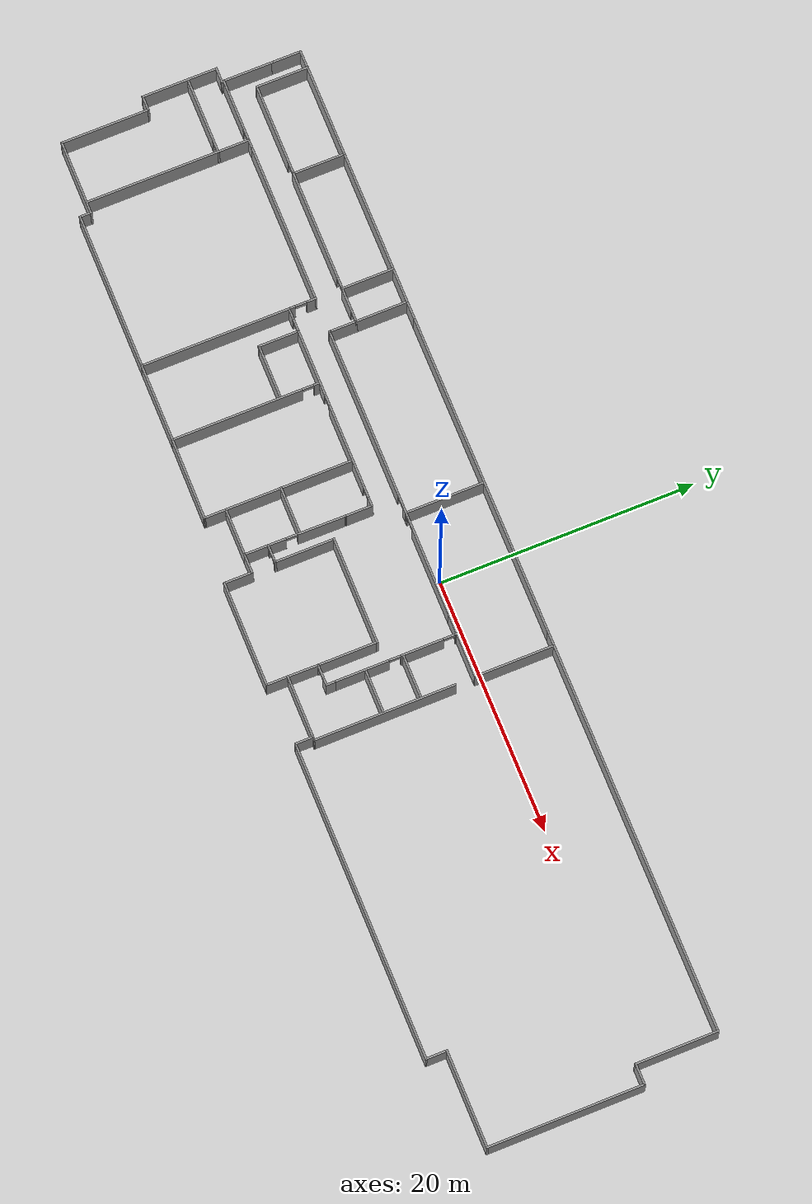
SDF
<?xml version='1.0'?>
<sdf version='1.7'>
  <model name='SMU_4th_Floor'>
    <pose>-0.970671 -4.58081 0 0 -0 0</pose>
    <link name='Wall_10'>
      <pose>-21.9301 2.97041 0 0 -0 1.5708</pose>
      <visual name='Wall_10_Visual_0'>
        <pose>-0.849622 0 1.25 0 -0 0</pose>
        <geometry>
          <box>
            <size>0.550756 0.15 2.5</size>
          </box>
        </geometry>
        <material>
          <script>
            <uri>file://media/materials/scripts/gazebo.material</uri>
            <name>Gazebo/Grey</name>
          </script>
          <ambient>1 1 1 1</ambient>
        </material>
        <meta>
          <layer>0</layer>
        </meta>
      </visual>
      <collision name='Wall_10_Collision_0'>
        <geometry>
          <box>
            <size>0.550756 0.15 2.5</size>
          </box>
        </geometry>
        <pose>-0.849622 0 1.25 0 -0 0</pose>
      </collision>
      <visual name='Wall_10_Visual_1'>
        <pose>0.725378 0 1.25 0 -0 0</pose>
        <geometry>
          <box>
            <size>0.799244 0.15 2.5</size>
          </box>
        </geometry>
        <material>
          <script>
            <uri>file://media/materials/scripts/gazebo.material</uri>
            <name>Gazebo/Grey</name>
          </script>
          <ambient>1 1 1 1</ambient>
        </material>
        <meta>
          <layer>0</layer>
        </meta>
      </visual>
      <collision name='Wall_10_Collision_1'>
        <geometry>
          <box>
            <size>0.799244 0.15 2.5</size>
          </box>
        </geometry>
        <pose>0.725378 0 1.25 0 -0 0</pose>
      </collision>
      <visual name='Wall_10_Visual_2'>
        <pose>-0.124244 0 2.25 0 -0 0</pose>
        <geometry>
          <box>
            <size>0.9 0.15 0.5</size>
          </box>
        </geometry>
        <material>
          <script>
            <uri>file://media/materials/scripts/gazebo.material</uri>
            <name>Gazebo/Grey</name>
          </script>
          <ambient>1 1 1 1</ambient>
        </material>
        <meta>
          <layer>0</layer>
        </meta>
      </visual>
      <collision name='Wall_10_Collision_2'>
        <geometry>
          <box>
            <size>0.9 0.15 0.5</size>
          </box>
        </geometry>
        <pose>-0.124244 0 2.25 0 -0 0</pose>
      </collision>
    </link>
    <link name='Wall_101'>
      <collision name='Wall_101_Collision'>
        <geometry>
          <box>
            <size>1.5 0.15 2.5</size>
          </box>
        </geometry>
        <pose>0 0 1.25 0 -0 0</pose>
      </collision>
      <visual name='Wall_101_Visual'>
        <pose>0 0 1.25 0 -0 0</pose>
        <geometry>
          <box>
            <size>1.5 0.15 2.5</size>
          </box>
        </geometry>
        <material>
          <script>
            <uri>file://media/materials/scripts/gazebo.material</uri>
            <name>Gazebo/Grey</name>
          </script>
          <ambient>1 1 1 1</ambient>
        </material>
        <meta>
          <layer>0</layer>
        </meta>
      </visual>
      <pose>8.74333 -9.19549 0 0 -0 1.5708</pose>
    </link>
    <link name='Wall_102'>
      <collision name='Wall_102_Collision'>
        <geometry>
          <box>
            <size>5 0.15 2.5</size>
          </box>
        </geometry>
        <pose>0 0 1.25 0 -0 0</pose>
      </collision>
      <visual name='Wall_102_Visual'>
        <pose>0 0 1.25 0 -0 0</pose>
        <geometry>
          <box>
            <size>5 0.15 2.5</size>
          </box>
        </geometry>
        <material>
          <script>
            <uri>file://media/materials/scripts/gazebo.material</uri>
            <name>Gazebo/Grey</name>
          </script>
          <ambient>1 1 1 1</ambient>
        </material>
        <meta>
          <layer>0</layer>
        </meta>
      </visual>
      <pose>6.31833 -8.52049 0 0 -0 3.14159</pose>
    </link>
    <link name='Wall_103'>
      <collision name='Wall_103_Collision'>
        <geometry>
          <box>
            <size>2.49105 0.15 2.5</size>
          </box>
        </geometry>
        <pose>0 0 1.25 0 -0 0</pose>
      </collision>
      <visual name='Wall_103_Visual'>
        <pose>0 0 1.25 0 -0 0</pose>
        <geometry>
          <box>
            <size>2.49105 0.15 2.5</size>
          </box>
        </geometry>
        <material>
          <script>
            <uri>file://media/materials/scripts/gazebo.material</uri>
            <name>Gazebo/Grey</name>
          </script>
          <ambient>1 1 1 1</ambient>
        </material>
        <meta>
          <layer>0</layer>
        </meta>
      </visual>
      <pose>3.90663 -7.35004 0 0 -0 1.55943</pose>
    </link>
    <link name='Wall_105'>
      <collision name='Wall_105_Collision'>
        <geometry>
          <box>
            <size>6.25 0.15 2.5</size>
          </box>
        </geometry>
        <pose>0 0 1.25 0 -0 0</pose>
      </collision>
      <visual name='Wall_105_Visual'>
        <pose>0 0 1.25 0 -0 0</pose>
        <geometry>
          <box>
            <size>6.25 0.15 2.5</size>
          </box>
        </geometry>
        <material>
          <script>
            <uri>file://media/materials/scripts/gazebo.material</uri>
            <name>Gazebo/Grey</name>
          </script>
          <ambient>1 1 1 1</ambient>
        </material>
        <meta>
          <layer>0</layer>
        </meta>
      </visual>
      <pose>-4.29599 7.06809 0 0 -0 -1.5708</pose>
    </link>
    <link name='Wall_107'>
      <collision name='Wall_107_Collision'>
        <geometry>
          <box>
            <size>1.6 0.15 2.5</size>
          </box>
        </geometry>
        <pose>0 0 1.25 0 -0 0</pose>
      </collision>
      <visual name='Wall_107_Visual'>
        <pose>0 0 1.25 0 -0 0</pose>
        <geometry>
          <box>
            <size>1.6 0.15 2.5</size>
          </box>
        </geometry>
        <material>
          <script>
            <uri>file://media/materials/scripts/gazebo.material</uri>
            <name>Gazebo/Grey</name>
          </script>
          <ambient>1 1 1 1</ambient>
        </material>
        <meta>
          <layer>0</layer>
        </meta>
      </visual>
      <pose>-5.05507 -8.02959 0 0 -0 0</pose>
    </link>
    <link name='Wall_109'>
      <collision name='Wall_109_Collision'>
        <geometry>
          <box>
            <size>2.3 0.15 2.5</size>
          </box>
        </geometry>
        <pose>0 0 1.25 0 -0 0</pose>
      </collision>
      <visual name='Wall_109_Visual'>
        <pose>0 0 1.25 0 -0 0</pose>
        <geometry>
          <box>
            <size>2.3 0.15 2.5</size>
          </box>
        </geometry>
        <material>
          <script>
            <uri>file://media/materials/scripts/gazebo.material</uri>
            <name>Gazebo/Grey</name>
          </script>
          <ambient>1 1 1 1</ambient>
        </material>
        <meta>
          <layer>0</layer>
        </meta>
      </visual>
      <pose>-4.33007 -9.10459 0 0 -0 -1.5708</pose>
    </link>
    <link name='Wall_11'>
      <collision name='Wall_11_Collision'>
        <geometry>
          <box>
            <size>12.75 0.15 2.5</size>
          </box>
        </geometry>
        <pose>0 0 1.25 0 -0 0</pose>
      </collision>
      <visual name='Wall_11_Visual'>
        <pose>0 0 1.25 0 -0 0</pose>
        <geometry>
          <box>
            <size>12.75 0.15 2.5</size>
          </box>
        </geometry>
        <material>
          <script>
            <uri>file://media/materials/scripts/gazebo.material</uri>
            <name>Gazebo/Grey</name>
          </script>
          <ambient>1 1 1 1</ambient>
        </material>
        <meta>
          <layer>0</layer>
        </meta>
      </visual>
      <pose>-28.2301 4.02041 0 0 -0 3.14159</pose>
    </link>
    <link name='Wall_111'>
      <collision name='Wall_111_Collision'>
        <geometry>
          <box>
            <size>8.3 0.15 2.5</size>
          </box>
        </geometry>
        <pose>0 0 1.25 0 -0 0</pose>
      </collision>
      <visual name='Wall_111_Visual'>
        <pose>0 0 1.25 0 -0 0</pose>
        <geometry>
          <box>
            <size>8.3 0.15 2.5</size>
          </box>
        </geometry>
        <material>
          <script>
            <uri>file://media/materials/scripts/gazebo.material</uri>
            <name>Gazebo/Grey</name>
          </script>
          <ambient>1 1 1 1</ambient>
        </material>
        <meta>
          <layer>0</layer>
        </meta>
      </visual>
      <pose>-0.255066 -10.1796 0 0 -0 0</pose>
    </link>
    <link name='Wall_113'>
      <collision name='Wall_113_Collision'>
        <geometry>
          <box>
            <size>1.8 0.15 2.5</size>
          </box>
        </geometry>
        <pose>0 0 1.25 0 -0 0</pose>
      </collision>
      <visual name='Wall_113_Visual'>
        <pose>0 0 1.25 0 -0 0</pose>
        <geometry>
          <box>
            <size>1.8 0.15 2.5</size>
          </box>
        </geometry>
        <material>
          <script>
            <uri>file://media/materials/scripts/gazebo.material</uri>
            <name>Gazebo/Grey</name>
          </script>
          <ambient>1 1 1 1</ambient>
        </material>
        <meta>
          <layer>0</layer>
        </meta>
      </visual>
      <pose>3.89333 -9.34549 0 0 -0 -1.5708</pose>
    </link>
    <link name='Wall_115'>
      <collision name='Wall_115_Collision'>
        <geometry>
          <box>
            <size>11.11 0.15 2.5</size>
          </box>
        </geometry>
        <pose>0 0 1.25 0 -0 0</pose>
      </collision>
      <visual name='Wall_115_Visual'>
        <pose>0 0 1.25 0 -0 0</pose>
        <geometry>
          <box>
            <size>11.11 0.15 2.5</size>
          </box>
        </geometry>
        <material>
          <script>
            <uri>file://media/materials/scripts/gazebo.material</uri>
            <name>Gazebo/Grey</name>
          </script>
          <ambient>1 1 1 1</ambient>
        </material>
        <meta>
          <layer>0</layer>
        </meta>
      </visual>
      <pose>8.99588 -3.03503 0 0 -0 -1.5708</pose>
    </link>
    <link name='Wall_119'>
      <collision name='Wall_119_Collision'>
        <geometry>
          <box>
            <size>0.402607 0.15 2.5</size>
          </box>
        </geometry>
        <pose>0 0 1.25 0 -0 0</pose>
      </collision>
      <visual name='Wall_119_Visual'>
        <pose>0 0 1.25 0 -0 0</pose>
        <geometry>
          <box>
            <size>0.402607 0.15 2.5</size>
          </box>
        </geometry>
        <material>
          <script>
            <uri>file://media/materials/scripts/gazebo.material</uri>
            <name>Gazebo/Grey</name>
          </script>
          <ambient>1 1 1 1</ambient>
        </material>
        <meta>
          <layer>0</layer>
        </meta>
      </visual>
      <pose>8.86961 -8.51776 0 0 -0 0.02159</pose>
    </link>
    <link name='Wall_122'>
      <collision name='Wall_122_Collision'>
        <geometry>
          <box>
            <size>3.5 0.15 2.5</size>
          </box>
        </geometry>
        <pose>0 0 1.25 0 -0 0</pose>
      </collision>
      <visual name='Wall_122_Visual'>
        <pose>0 0 1.25 0 -0 0</pose>
        <geometry>
          <box>
            <size>3.5 0.15 2.5</size>
          </box>
        </geometry>
        <material>
          <script>
            <uri>file://media/materials/scripts/gazebo.material</uri>
            <name>Gazebo/Grey</name>
          </script>
          <ambient>1 1 1 1</ambient>
        </material>
        <meta>
          <layer>0</layer>
        </meta>
      </visual>
      <pose>7.22208 -3.13125 0 0 -0 0</pose>
    </link>
    <link name='Wall_124'>
      <collision name='Wall_124_Collision'>
        <geometry>
          <box>
            <size>3.5 0.15 2.5</size>
          </box>
        </geometry>
        <pose>0 0 1.25 0 -0 0</pose>
      </collision>
      <visual name='Wall_124_Visual'>
        <pose>0 0 1.25 0 -0 0</pose>
        <geometry>
          <box>
            <size>3.5 0.15 2.5</size>
          </box>
        </geometry>
        <material>
          <script>
            <uri>file://media/materials/scripts/gazebo.material</uri>
            <name>Gazebo/Grey</name>
          </script>
          <ambient>1 1 1 1</ambient>
        </material>
        <meta>
          <layer>0</layer>
        </meta>
      </visual>
      <pose>7.28373 -0.193726 0 0 -0 3.14159</pose>
    </link>
    <link name='Wall_126'>
      <collision name='Wall_126_Collision'>
        <geometry>
          <box>
            <size>3.6 0.15 2.5</size>
          </box>
        </geometry>
        <pose>0 0 1.25 0 -0 0</pose>
      </collision>
      <visual name='Wall_126_Visual'>
        <pose>0 0 1.25 0 -0 0</pose>
        <geometry>
          <box>
            <size>3.6 0.15 2.5</size>
          </box>
        </geometry>
        <material>
          <script>
            <uri>file://media/materials/scripts/gazebo.material</uri>
            <name>Gazebo/Grey</name>
          </script>
          <ambient>1 1 1 1</ambient>
        </material>
        <meta>
          <layer>0</layer>
        </meta>
      </visual>
      <pose>7.24493 4.02041 0 0 -0 0</pose>
    </link>
    <link name='Wall_129'>
      <collision name='Wall_129_Collision'>
        <geometry>
          <box>
            <size>6.25 0.15 2.5</size>
          </box>
        </geometry>
        <pose>0 0 1.25 0 -0 0</pose>
      </collision>
      <visual name='Wall_129_Visual'>
        <pose>0 0 1.25 0 -0 0</pose>
        <geometry>
          <box>
            <size>6.25 0.15 2.5</size>
          </box>
        </geometry>
        <material>
          <script>
            <uri>file://media/materials/scripts/gazebo.material</uri>
            <name>Gazebo/Grey</name>
          </script>
          <ambient>1 1 1 1</ambient>
        </material>
        <meta>
          <layer>0</layer>
        </meta>
      </visual>
      <pose>8.96993 7.07041 0 0 -0 1.5708</pose>
    </link>
    <link name='Wall_13'>
      <pose>-37.3301 4.02041 0 0 -0 3.14159</pose>
      <visual name='Wall_13_Visual_0'>
        <pose>-2.49577 0 1.25 0 -0 0</pose>
        <geometry>
          <box>
            <size>0.758458 0.15 2.5</size>
          </box>
        </geometry>
        <material>
          <script>
            <uri>file://media/materials/scripts/gazebo.material</uri>
            <name>Gazebo/Grey</name>
          </script>
          <ambient>1 1 1 1</ambient>
        </material>
        <meta>
          <layer>0</layer>
        </meta>
      </visual>
      <collision name='Wall_13_Collision_0'>
        <geometry>
          <box>
            <size>0.758458 0.15 2.5</size>
          </box>
        </geometry>
        <pose>-2.49577 0 1.25 0 -0 0</pose>
      </collision>
      <visual name='Wall_13_Visual_1'>
        <pose>0.829229 0 1.25 0 -0 0</pose>
        <geometry>
          <box>
            <size>4.09154 0.15 2.5</size>
          </box>
        </geometry>
        <material>
          <script>
            <uri>file://media/materials/scripts/gazebo.material</uri>
            <name>Gazebo/Grey</name>
          </script>
          <ambient>1 1 1 1</ambient>
        </material>
        <meta>
          <layer>0</layer>
        </meta>
      </visual>
      <collision name='Wall_13_Collision_1'>
        <geometry>
          <box>
            <size>4.09154 0.15 2.5</size>
          </box>
        </geometry>
        <pose>0.829229 0 1.25 0 -0 0</pose>
      </collision>
      <visual name='Wall_13_Visual_2'>
        <pose>-1.66654 0 2.25 0 -0 0</pose>
        <geometry>
          <box>
            <size>0.9 0.15 0.5</size>
          </box>
        </geometry>
        <material>
          <script>
            <uri>file://media/materials/scripts/gazebo.material</uri>
            <name>Gazebo/Grey</name>
          </script>
          <ambient>1 1 1 1</ambient>
        </material>
        <meta>
          <layer>0</layer>
        </meta>
      </visual>
      <collision name='Wall_13_Collision_2'>
        <geometry>
          <box>
            <size>0.9 0.15 0.5</size>
          </box>
        </geometry>
        <pose>-1.66654 0 2.25 0 -0 0</pose>
      </collision>
    </link>
    <link name='Wall_14'>
      <collision name='Wall_14_Collision'>
        <geometry>
          <box>
            <size>4 0.15 2.5</size>
          </box>
        </geometry>
        <pose>0 0 1.25 0 -0 0</pose>
      </collision>
      <visual name='Wall_14_Visual'>
        <pose>0 0 1.25 0 -0 0</pose>
        <geometry>
          <box>
            <size>4 0.15 2.5</size>
          </box>
        </geometry>
        <material>
          <script>
            <uri>file://media/materials/scripts/gazebo.material</uri>
            <name>Gazebo/Grey</name>
          </script>
          <ambient>1 1 1 1</ambient>
        </material>
        <meta>
          <layer>0</layer>
        </meta>
      </visual>
      <pose>-40.1301 5.94541 0 0 -0 1.5708</pose>
    </link>
    <link name='Wall_16'>
      <collision name='Wall_16_Collision'>
        <geometry>
          <box>
            <size>2.4325 0.15 2.5</size>
          </box>
        </geometry>
        <pose>0 0 1.25 0 -0 0</pose>
      </collision>
      <visual name='Wall_16_Visual'>
        <pose>0 0 1.25 0 -0 0</pose>
        <geometry>
          <box>
            <size>2.4325 0.15 2.5</size>
          </box>
        </geometry>
        <material>
          <script>
            <uri>file://media/materials/scripts/gazebo.material</uri>
            <name>Gazebo/Grey</name>
          </script>
          <ambient>1 1 1 1</ambient>
        </material>
        <meta>
          <layer>0</layer>
        </meta>
      </visual>
      <pose>-40.1301 9.01166 0 0 -0 1.5708</pose>
    </link>
    <link name='Wall_17'>
      <collision name='Wall_17_Collision'>
        <geometry>
          <box>
            <size>1.5 0.15 2.5</size>
          </box>
        </geometry>
        <pose>0 0 1.25 0 -0 0</pose>
      </collision>
      <visual name='Wall_17_Visual'>
        <pose>0 0 1.25 0 -0 0</pose>
        <geometry>
          <box>
            <size>1.5 0.15 2.5</size>
          </box>
        </geometry>
        <material>
          <script>
            <uri>file://media/materials/scripts/gazebo.material</uri>
            <name>Gazebo/Grey</name>
          </script>
          <ambient>1 1 1 1</ambient>
        </material>
        <meta>
          <layer>0</layer>
        </meta>
      </visual>
      <pose>-39.4551 10.1377 0 0 -0 0</pose>
    </link>
    <link name='Wall_18'>
      <collision name='Wall_18_Collision'>
        <geometry>
          <box>
            <size>4.1825 0.15 2.5</size>
          </box>
        </geometry>
        <pose>0 0 1.25 0 -0 0</pose>
      </collision>
      <visual name='Wall_18_Visual'>
        <pose>0 0 1.25 0 -0 0</pose>
        <geometry>
          <box>
            <size>4.1825 0.15 2.5</size>
          </box>
        </geometry>
        <material>
          <script>
            <uri>file://media/materials/scripts/gazebo.material</uri>
            <name>Gazebo/Grey</name>
          </script>
          <ambient>1 1 1 1</ambient>
        </material>
        <meta>
          <layer>0</layer>
        </meta>
      </visual>
      <pose>-38.7801 8.13666 0 0 -0 -1.5708</pose>
    </link>
    <link name='Wall_19'>
      <pose>-28.9801 6.12041 0 0 -0 0</pose>
      <visual name='Wall_19_Visual_0'>
        <pose>-6.69762 0 1.25 0 -0 0</pose>
        <geometry>
          <box>
            <size>6.35476 0.15 2.5</size>
          </box>
        </geometry>
        <material>
          <script>
            <uri>file://media/materials/scripts/gazebo.material</uri>
            <name>Gazebo/Grey</name>
          </script>
          <ambient>1 1 1 1</ambient>
        </material>
        <meta>
          <layer>0</layer>
        </meta>
      </visual>
      <collision name='Wall_19_Collision_0'>
        <geometry>
          <box>
            <size>6.35476 0.15 2.5</size>
          </box>
        </geometry>
        <pose>-6.69762 0 1.25 0 -0 0</pose>
      </collision>
      <visual name='Wall_19_Visual_1'>
        <pose>1.75972 0 1.25 0 -0 0</pose>
        <geometry>
          <box>
            <size>8.75991 0.15 2.5</size>
          </box>
        </geometry>
        <material>
          <script>
            <uri>file://media/materials/scripts/gazebo.material</uri>
            <name>Gazebo/Grey</name>
          </script>
          <ambient>1 1 1 1</ambient>
        </material>
        <meta>
          <layer>0</layer>
        </meta>
      </visual>
      <collision name='Wall_19_Collision_1'>
        <geometry>
          <box>
            <size>8.75991 0.15 2.5</size>
          </box>
        </geometry>
        <pose>1.75972 0 1.25 0 -0 0</pose>
      </collision>
      <visual name='Wall_19_Visual_2'>
        <pose>7.94293 0 1.25 0 -0 0</pose>
        <geometry>
          <box>
            <size>1.80652 0.15 2.5</size>
          </box>
        </geometry>
        <material>
          <script>
            <uri>file://media/materials/scripts/gazebo.material</uri>
            <name>Gazebo/Grey</name>
          </script>
          <ambient>1 1 1 1</ambient>
        </material>
        <meta>
          <layer>0</layer>
        </meta>
      </visual>
      <collision name='Wall_19_Collision_2'>
        <geometry>
          <box>
            <size>1.80652 0.15 2.5</size>
          </box>
        </geometry>
        <pose>7.94293 0 1.25 0 -0 0</pose>
      </collision>
      <visual name='Wall_19_Visual_3'>
        <pose>9.8106 0 1.25 0 -0 0</pose>
        <geometry>
          <box>
            <size>0.128804 0.15 2.5</size>
          </box>
        </geometry>
        <material>
          <script>
            <uri>file://media/materials/scripts/gazebo.material</uri>
            <name>Gazebo/Grey</name>
          </script>
          <ambient>1 1 1 1</ambient>
        </material>
        <meta>
          <layer>0</layer>
        </meta>
      </visual>
      <collision name='Wall_19_Collision_3'>
        <geometry>
          <box>
            <size>0.128804 0.15 2.5</size>
          </box>
        </geometry>
        <pose>9.8106 0 1.25 0 -0 0</pose>
      </collision>
      <visual name='Wall_19_Visual_4'>
        <pose>-3.07024 0 2.25 0 -0 0</pose>
        <geometry>
          <box>
            <size>0.9 0.15 0.5</size>
          </box>
        </geometry>
        <material>
          <script>
            <uri>file://media/materials/scripts/gazebo.material</uri>
            <name>Gazebo/Grey</name>
          </script>
          <ambient>1 1 1 1</ambient>
        </material>
        <meta>
          <layer>0</layer>
        </meta>
      </visual>
      <collision name='Wall_19_Collision_4'>
        <geometry>
          <box>
            <size>0.9 0.15 0.5</size>
          </box>
        </geometry>
        <pose>-3.07024 0 2.25 0 -0 0</pose>
      </collision>
      <visual name='Wall_19_Visual_5'>
        <pose>6.58967 0 2.25 0 -0 0</pose>
        <geometry>
          <box>
            <size>0.9 0.15 0.5</size>
          </box>
        </geometry>
        <material>
          <script>
            <uri>file://media/materials/scripts/gazebo.material</uri>
            <name>Gazebo/Grey</name>
          </script>
          <ambient>1 1 1 1</ambient>
        </material>
        <meta>
          <layer>0</layer>
        </meta>
      </visual>
      <collision name='Wall_19_Collision_5'>
        <geometry>
          <box>
            <size>0.9 0.15 0.5</size>
          </box>
        </geometry>
        <pose>6.58967 0 2.25 0 -0 0</pose>
      </collision>
      <visual name='Wall_19_Visual_6'>
        <pose>9.2962 0 2.25 0 -0 0</pose>
        <geometry>
          <box>
            <size>0.9 0.15 0.5</size>
          </box>
        </geometry>
        <material>
          <script>
            <uri>file://media/materials/scripts/gazebo.material</uri>
            <name>Gazebo/Grey</name>
          </script>
          <ambient>1 1 1 1</ambient>
        </material>
        <meta>
          <layer>0</layer>
        </meta>
      </visual>
      <collision name='Wall_19_Collision_6'>
        <geometry>
          <box>
            <size>0.9 0.15 0.5</size>
          </box>
        </geometry>
        <pose>9.2962 0 2.25 0 -0 0</pose>
      </collision>
    </link>
    <link name='Wall_21'>
      <collision name='Wall_21_Collision'>
        <geometry>
          <box>
            <size>2.25 0.15 2.5</size>
          </box>
        </geometry>
        <pose>0 0 1.25 0 -0 0</pose>
      </collision>
      <visual name='Wall_21_Visual'>
        <pose>0 0 1.25 0 -0 0</pose>
        <geometry>
          <box>
            <size>2.25 0.15 2.5</size>
          </box>
        </geometry>
        <material>
          <script>
            <uri>file://media/materials/scripts/gazebo.material</uri>
            <name>Gazebo/Grey</name>
          </script>
          <ambient>1 1 1 1</ambient>
        </material>
        <meta>
          <layer>0</layer>
        </meta>
      </visual>
      <pose>-19.1801 5.07041 0 0 -0 -1.5708</pose>
    </link>
    <link name='Wall_22'>
      <pose>-7.63007 4.02041 0 0 -0 0</pose>
      <visual name='Wall_22_Visual_0'>
        <pose>-4.87483 0 1.25 0 -0 0</pose>
        <geometry>
          <box>
            <size>13.5003 0.15 2.5</size>
          </box>
        </geometry>
        <material>
          <script>
            <uri>file://media/materials/scripts/gazebo.material</uri>
            <name>Gazebo/Grey</name>
          </script>
          <ambient>1 1 1 1</ambient>
        </material>
        <meta>
          <layer>0</layer>
        </meta>
      </visual>
      <collision name='Wall_22_Collision_0'>
        <geometry>
          <box>
            <size>13.5003 0.15 2.5</size>
          </box>
        </geometry>
        <pose>-4.87483 0 1.25 0 -0 0</pose>
      </collision>
      <visual name='Wall_22_Visual_1'>
        <pose>3.21141 0 1.25 0 -0 0</pose>
        <geometry>
          <box>
            <size>0.87215 0.15 2.5</size>
          </box>
        </geometry>
        <material>
          <script>
            <uri>file://media/materials/scripts/gazebo.material</uri>
            <name>Gazebo/Grey</name>
          </script>
          <ambient>1 1 1 1</ambient>
        </material>
        <meta>
          <layer>0</layer>
        </meta>
      </visual>
      <collision name='Wall_22_Collision_1'>
        <geometry>
          <box>
            <size>0.87215 0.15 2.5</size>
          </box>
        </geometry>
        <pose>3.21141 0 1.25 0 -0 0</pose>
      </collision>
      <visual name='Wall_22_Visual_2'>
        <pose>8.08624 0 1.25 0 -0 0</pose>
        <geometry>
          <box>
            <size>7.07751 0.15 2.5</size>
          </box>
        </geometry>
        <material>
          <script>
            <uri>file://media/materials/scripts/gazebo.material</uri>
            <name>Gazebo/Grey</name>
          </script>
          <ambient>1 1 1 1</ambient>
        </material>
        <meta>
          <layer>0</layer>
        </meta>
      </visual>
      <collision name='Wall_22_Collision_2'>
        <geometry>
          <box>
            <size>7.07751 0.15 2.5</size>
          </box>
        </geometry>
        <pose>8.08624 0 1.25 0 -0 0</pose>
      </collision>
      <visual name='Wall_22_Visual_3'>
        <pose>2.32534 0 2.25 0 -0 0</pose>
        <geometry>
          <box>
            <size>0.9 0.15 0.5</size>
          </box>
        </geometry>
        <material>
          <script>
            <uri>file://media/materials/scripts/gazebo.material</uri>
            <name>Gazebo/Grey</name>
          </script>
          <ambient>1 1 1 1</ambient>
        </material>
        <meta>
          <layer>0</layer>
        </meta>
      </visual>
      <collision name='Wall_22_Collision_3'>
        <geometry>
          <box>
            <size>0.9 0.15 0.5</size>
          </box>
        </geometry>
        <pose>2.32534 0 2.25 0 -0 0</pose>
      </collision>
      <visual name='Wall_22_Visual_4'>
        <pose>4.09749 0 2.25 0 -0 0</pose>
        <geometry>
          <box>
            <size>0.9 0.15 0.5</size>
          </box>
        </geometry>
        <material>
          <script>
            <uri>file://media/materials/scripts/gazebo.material</uri>
            <name>Gazebo/Grey</name>
          </script>
          <ambient>1 1 1 1</ambient>
        </material>
        <meta>
          <layer>0</layer>
        </meta>
      </visual>
      <collision name='Wall_22_Collision_4'>
        <geometry>
          <box>
            <size>0.9 0.15 0.5</size>
          </box>
        </geometry>
        <pose>4.09749 0 2.25 0 -0 0</pose>
      </collision>
    </link>
    <link name='Wall_24'>
      <collision name='Wall_24_Collision'>
        <geometry>
          <box>
            <size>1.75 0.15 2.5</size>
          </box>
        </geometry>
        <pose>0 0 1.25 0 -0 0</pose>
      </collision>
      <visual name='Wall_24_Visual'>
        <pose>0 0 1.25 0 -0 0</pose>
        <geometry>
          <box>
            <size>1.75 0.15 2.5</size>
          </box>
        </geometry>
        <material>
          <script>
            <uri>file://media/materials/scripts/gazebo.material</uri>
            <name>Gazebo/Grey</name>
          </script>
          <ambient>1 1 1 1</ambient>
        </material>
        <meta>
          <layer>0</layer>
        </meta>
      </visual>
      <pose>4.71993 4.02041 0 0 -0 0</pose>
    </link>
    <link name='Wall_26'>
      <pose>5.51994 -0.779592 0 0 -0 -1.5708</pose>
      <visual name='Wall_26_Visual_0'>
        <pose>-4.74915 0 1.25 0 -0 0</pose>
        <geometry>
          <box>
            <size>0.251694 0.15 2.5</size>
          </box>
        </geometry>
        <material>
          <script>
            <uri>file://media/materials/scripts/gazebo.material</uri>
            <name>Gazebo/Grey</name>
          </script>
          <ambient>1 1 1 1</ambient>
        </material>
        <meta>
          <layer>0</layer>
        </meta>
      </visual>
      <collision name='Wall_26_Collision_0'>
        <geometry>
          <box>
            <size>0.251694 0.15 2.5</size>
          </box>
        </geometry>
        <pose>-4.74915 0 1.25 0 -0 0</pose>
      </collision>
      <visual name='Wall_26_Visual_1'>
        <pose>-2.05701 0 1.25 0 -0 0</pose>
        <geometry>
          <box>
            <size>3.33259 0.15 2.5</size>
          </box>
        </geometry>
        <material>
          <script>
            <uri>file://media/materials/scripts/gazebo.material</uri>
            <name>Gazebo/Grey</name>
          </script>
          <ambient>1 1 1 1</ambient>
        </material>
        <meta>
          <layer>0</layer>
        </meta>
      </visual>
      <collision name='Wall_26_Collision_1'>
        <geometry>
          <box>
            <size>3.33259 0.15 2.5</size>
          </box>
        </geometry>
        <pose>-2.05701 0 1.25 0 -0 0</pose>
      </collision>
      <visual name='Wall_26_Visual_2'>
        <pose>2.69215 0 1.25 0 -0 0</pose>
        <geometry>
          <box>
            <size>4.36571 0.15 2.5</size>
          </box>
        </geometry>
        <material>
          <script>
            <uri>file://media/materials/scripts/gazebo.material</uri>
            <name>Gazebo/Grey</name>
          </script>
          <ambient>1 1 1 1</ambient>
        </material>
        <meta>
          <layer>0</layer>
        </meta>
      </visual>
      <collision name='Wall_26_Collision_2'>
        <geometry>
          <box>
            <size>4.36571 0.15 2.5</size>
          </box>
        </geometry>
        <pose>2.69215 0 1.25 0 -0 0</pose>
      </collision>
      <visual name='Wall_26_Visual_3'>
        <pose>-4.17331 0 2.25 0 -0 0</pose>
        <geometry>
          <box>
            <size>0.9 0.15 0.5</size>
          </box>
        </geometry>
        <material>
          <script>
            <uri>file://media/materials/scripts/gazebo.material</uri>
            <name>Gazebo/Grey</name>
          </script>
          <ambient>1 1 1 1</ambient>
        </material>
        <meta>
          <layer>0</layer>
        </meta>
      </visual>
      <collision name='Wall_26_Collision_3'>
        <geometry>
          <box>
            <size>0.9 0.15 0.5</size>
          </box>
        </geometry>
        <pose>-4.17331 0 2.25 0 -0 0</pose>
      </collision>
      <visual name='Wall_26_Visual_4'>
        <pose>0.059289 0 2.25 0 -0 0</pose>
        <geometry>
          <box>
            <size>0.9 0.15 0.5</size>
          </box>
        </geometry>
        <material>
          <script>
            <uri>file://media/materials/scripts/gazebo.material</uri>
            <name>Gazebo/Grey</name>
          </script>
          <ambient>1 1 1 1</ambient>
        </material>
        <meta>
          <layer>0</layer>
        </meta>
      </visual>
      <collision name='Wall_26_Collision_4'>
        <geometry>
          <box>
            <size>0.9 0.15 0.5</size>
          </box>
        </geometry>
        <pose>0.059289 0 2.25 0 -0 0</pose>
      </collision>
    </link>
    <link name='Wall_34'>
      <collision name='Wall_34_Collision'>
        <geometry>
          <box>
            <size>0.75 0.15 2.5</size>
          </box>
        </geometry>
        <pose>0 0 1.25 0 -0 0</pose>
      </collision>
      <visual name='Wall_34_Visual'>
        <pose>0 0 1.25 0 -0 0</pose>
        <geometry>
          <box>
            <size>0.75 0.15 2.5</size>
          </box>
        </geometry>
        <material>
          <script>
            <uri>file://media/materials/scripts/gazebo.material</uri>
            <name>Gazebo/Grey</name>
          </script>
          <ambient>1 1 1 1</ambient>
        </material>
        <meta>
          <layer>0</layer>
        </meta>
      </visual>
      <pose>5.51994 -5.87959 0 0 -0 -1.5708</pose>
    </link>
    <link name='Wall_35'>
      <pose>4.71993 -6.17959 0 0 -0 3.14159</pose>
      <visual name='Wall_35_Visual_0'>
        <pose>-0.547736 0 1.25 0 -0 0</pose>
        <geometry>
          <box>
            <size>0.654529 0.15 2.5</size>
          </box>
        </geometry>
        <material>
          <script>
            <uri>file://media/materials/scripts/gazebo.material</uri>
            <name>Gazebo/Grey</name>
          </script>
          <ambient>1 1 1 1</ambient>
        </material>
        <meta>
          <layer>0</layer>
        </meta>
      </visual>
      <collision name='Wall_35_Collision_0'>
        <geometry>
          <box>
            <size>0.654529 0.15 2.5</size>
          </box>
        </geometry>
        <pose>-0.547736 0 1.25 0 -0 0</pose>
      </collision>
      <visual name='Wall_35_Visual_1'>
        <pose>0.777264 0 1.25 0 -0 0</pose>
        <geometry>
          <box>
            <size>0.195471 0.15 2.5</size>
          </box>
        </geometry>
        <material>
          <script>
            <uri>file://media/materials/scripts/gazebo.material</uri>
            <name>Gazebo/Grey</name>
          </script>
          <ambient>1 1 1 1</ambient>
        </material>
        <meta>
          <layer>0</layer>
        </meta>
      </visual>
      <collision name='Wall_35_Collision_1'>
        <geometry>
          <box>
            <size>0.195471 0.15 2.5</size>
          </box>
        </geometry>
        <pose>0.777264 0 1.25 0 -0 0</pose>
      </collision>
      <visual name='Wall_35_Visual_2'>
        <pose>0.229529 0 2.25 0 -0 0</pose>
        <geometry>
          <box>
            <size>0.9 0.15 0.5</size>
          </box>
        </geometry>
        <material>
          <script>
            <uri>file://media/materials/scripts/gazebo.material</uri>
            <name>Gazebo/Grey</name>
          </script>
          <ambient>1 1 1 1</ambient>
        </material>
        <meta>
          <layer>0</layer>
        </meta>
      </visual>
      <collision name='Wall_35_Collision_2'>
        <geometry>
          <box>
            <size>0.9 0.15 0.5</size>
          </box>
        </geometry>
        <pose>0.229529 0 2.25 0 -0 0</pose>
      </collision>
    </link>
    <link name='Wall_36'>
      <collision name='Wall_36_Collision'>
        <geometry>
          <box>
            <size>4.75 0.15 2.5</size>
          </box>
        </geometry>
        <pose>0 0 1.25 0 -0 0</pose>
      </collision>
      <visual name='Wall_36_Visual'>
        <pose>0 0 1.25 0 -0 0</pose>
        <geometry>
          <box>
            <size>4.75 0.15 2.5</size>
          </box>
        </geometry>
        <material>
          <script>
            <uri>file://media/materials/scripts/gazebo.material</uri>
            <name>Gazebo/Grey</name>
          </script>
          <ambient>1 1 1 1</ambient>
        </material>
        <meta>
          <layer>0</layer>
        </meta>
      </visual>
      <pose>3.91994 -3.87959 0 0 -0 1.5708</pose>
    </link>
    <link name='Wall_37'>
      <collision name='Wall_37_Collision'>
        <geometry>
          <box>
            <size>8.5 0.15 2.5</size>
          </box>
        </geometry>
        <pose>0 0 1.25 0 -0 0</pose>
      </collision>
      <visual name='Wall_37_Visual'>
        <pose>0 0 1.25 0 -0 0</pose>
        <geometry>
          <box>
            <size>8.5 0.15 2.5</size>
          </box>
        </geometry>
        <material>
          <script>
            <uri>file://media/materials/scripts/gazebo.material</uri>
            <name>Gazebo/Grey</name>
          </script>
          <ambient>1 1 1 1</ambient>
        </material>
        <meta>
          <layer>0</layer>
        </meta>
      </visual>
      <pose>-0.255066 -1.57959 0 0 -0 3.14159</pose>
    </link>
    <link name='Wall_38'>
      <collision name='Wall_38_Collision'>
        <geometry>
          <box>
            <size>4.75 0.15 2.5</size>
          </box>
        </geometry>
        <pose>0 0 1.25 0 -0 0</pose>
      </collision>
      <visual name='Wall_38_Visual'>
        <pose>0 0 1.25 0 -0 0</pose>
        <geometry>
          <box>
            <size>4.75 0.15 2.5</size>
          </box>
        </geometry>
        <material>
          <script>
            <uri>file://media/materials/scripts/gazebo.material</uri>
            <name>Gazebo/Grey</name>
          </script>
          <ambient>1 1 1 1</ambient>
        </material>
        <meta>
          <layer>0</layer>
        </meta>
      </visual>
      <pose>-4.43007 -3.87959 0 0 -0 -1.5708</pose>
    </link>
    <link name='Wall_40'>
      <pose>-5.10506 -6.17959 0 0 -0 3.14159</pose>
      <visual name='Wall_40_Visual_0'>
        <pose>-0.626564 0 1.25 0 -0 0</pose>
        <geometry>
          <box>
            <size>0.246873 0.15 2.5</size>
          </box>
        </geometry>
        <material>
          <script>
            <uri>file://media/materials/scripts/gazebo.material</uri>
            <name>Gazebo/Grey</name>
          </script>
          <ambient>1 1 1 1</ambient>
        </material>
        <meta>
          <layer>0</layer>
        </meta>
      </visual>
      <collision name='Wall_40_Collision_0'>
        <geometry>
          <box>
            <size>0.246873 0.15 2.5</size>
          </box>
        </geometry>
        <pose>-0.626564 0 1.25 0 -0 0</pose>
      </collision>
      <visual name='Wall_40_Visual_1'>
        <pose>0.573436 0 1.25 0 -0 0</pose>
        <geometry>
          <box>
            <size>0.353127 0.15 2.5</size>
          </box>
        </geometry>
        <material>
          <script>
            <uri>file://media/materials/scripts/gazebo.material</uri>
            <name>Gazebo/Grey</name>
          </script>
          <ambient>1 1 1 1</ambient>
        </material>
        <meta>
          <layer>0</layer>
        </meta>
      </visual>
      <collision name='Wall_40_Collision_1'>
        <geometry>
          <box>
            <size>0.353127 0.15 2.5</size>
          </box>
        </geometry>
        <pose>0.573436 0 1.25 0 -0 0</pose>
      </collision>
      <visual name='Wall_40_Visual_2'>
        <pose>-0.053127 0 2.25 0 -0 0</pose>
        <geometry>
          <box>
            <size>0.9 0.15 0.5</size>
          </box>
        </geometry>
        <material>
          <script>
            <uri>file://media/materials/scripts/gazebo.material</uri>
            <name>Gazebo/Grey</name>
          </script>
          <ambient>1 1 1 1</ambient>
        </material>
        <meta>
          <layer>0</layer>
        </meta>
      </visual>
      <collision name='Wall_40_Collision_2'>
        <geometry>
          <box>
            <size>0.9 0.15 0.5</size>
          </box>
        </geometry>
        <pose>-0.053127 0 2.25 0 -0 0</pose>
      </collision>
    </link>
    <link name='Wall_41'>
      <pose>-5.75507 -3.17959 0 0 -0 1.56246</pose>
      <visual name='Wall_41_Visual_0'>
        <pose>-2.34959 0 1.25 0 -0 0</pose>
        <geometry>
          <box>
            <size>1.45103 0.15 2.5</size>
          </box>
        </geometry>
        <material>
          <script>
            <uri>file://media/materials/scripts/gazebo.material</uri>
            <name>Gazebo/Grey</name>
          </script>
          <ambient>1 1 1 1</ambient>
        </material>
        <meta>
          <layer>0</layer>
        </meta>
      </visual>
      <collision name='Wall_41_Collision_0'>
        <geometry>
          <box>
            <size>1.45103 0.15 2.5</size>
          </box>
        </geometry>
        <pose>-2.34959 0 1.25 0 -0 0</pose>
      </collision>
      <visual name='Wall_41_Visual_1'>
        <pose>1.17552 0 1.25 0 -0 0</pose>
        <geometry>
          <box>
            <size>3.79917 0.15 2.5</size>
          </box>
        </geometry>
        <material>
          <script>
            <uri>file://media/materials/scripts/gazebo.material</uri>
            <name>Gazebo/Grey</name>
          </script>
          <ambient>1 1 1 1</ambient>
        </material>
        <meta>
          <layer>0</layer>
        </meta>
      </visual>
      <collision name='Wall_41_Collision_1'>
        <geometry>
          <box>
            <size>3.79917 0.15 2.5</size>
          </box>
        </geometry>
        <pose>1.17552 0 1.25 0 -0 0</pose>
      </collision>
      <visual name='Wall_41_Visual_2'>
        <pose>-1.17407 0 2.25 0 -0 0</pose>
        <geometry>
          <box>
            <size>0.9 0.15 0.5</size>
          </box>
        </geometry>
        <material>
          <script>
            <uri>file://media/materials/scripts/gazebo.material</uri>
            <name>Gazebo/Grey</name>
          </script>
          <ambient>1 1 1 1</ambient>
        </material>
        <meta>
          <layer>0</layer>
        </meta>
      </visual>
      <collision name='Wall_41_Collision_2'>
        <geometry>
          <box>
            <size>0.9 0.15 0.5</size>
          </box>
        </geometry>
        <pose>-1.17407 0 2.25 0 -0 0</pose>
      </collision>
    </link>
    <link name='Wall_43'>
      <collision name='Wall_43_Collision'>
        <geometry>
          <box>
            <size>11.75 0.15 2.5</size>
          </box>
        </geometry>
        <pose>0 0 1.25 0 -0 0</pose>
      </collision>
      <visual name='Wall_43_Visual'>
        <pose>0 0 1.25 0 -0 0</pose>
        <geometry>
          <box>
            <size>11.75 0.15 2.5</size>
          </box>
        </geometry>
        <material>
          <script>
            <uri>file://media/materials/scripts/gazebo.material</uri>
            <name>Gazebo/Grey</name>
          </script>
          <ambient>1 1 1 1</ambient>
        </material>
        <meta>
          <layer>0</layer>
        </meta>
      </visual>
      <pose>-21.9301 -3.87959 0 0 -0 -1.5708</pose>
    </link>
    <link name='Wall_44'>
      <collision name='Wall_44_Collision'>
        <geometry>
          <box>
            <size>6.25 0.15 2.5</size>
          </box>
        </geometry>
        <pose>0 0 1.25 0 -0 0</pose>
      </collision>
      <visual name='Wall_44_Visual'>
        <pose>0 0 1.25 0 -0 0</pose>
        <geometry>
          <box>
            <size>6.25 0.15 2.5</size>
          </box>
        </geometry>
        <material>
          <script>
            <uri>file://media/materials/scripts/gazebo.material</uri>
            <name>Gazebo/Grey</name>
          </script>
          <ambient>1 1 1 1</ambient>
        </material>
        <meta>
          <layer>0</layer>
        </meta>
      </visual>
      <pose>-18.8801 -9.67959 0 0 -0 0</pose>
    </link>
    <link name='Wall_45'>
      <pose>-15.8301 -3.87959 0 0 -0 1.5708</pose>
      <visual name='Wall_45_Visual_0'>
        <pose>-0.742565 0 1.25 0 -0 0</pose>
        <geometry>
          <box>
            <size>10.2649 0.15 2.5</size>
          </box>
        </geometry>
        <material>
          <script>
            <uri>file://media/materials/scripts/gazebo.material</uri>
            <name>Gazebo/Grey</name>
          </script>
          <ambient>1 1 1 1</ambient>
        </material>
        <meta>
          <layer>0</layer>
        </meta>
      </visual>
      <collision name='Wall_45_Collision_0'>
        <geometry>
          <box>
            <size>10.2649 0.15 2.5</size>
          </box>
        </geometry>
        <pose>-0.742565 0 1.25 0 -0 0</pose>
      </collision>
      <visual name='Wall_45_Visual_1'>
        <pose>5.58244 0 1.25 0 -0 0</pose>
        <geometry>
          <box>
            <size>0.58513 0.15 2.5</size>
          </box>
        </geometry>
        <material>
          <script>
            <uri>file://media/materials/scripts/gazebo.material</uri>
            <name>Gazebo/Grey</name>
          </script>
          <ambient>1 1 1 1</ambient>
        </material>
        <meta>
          <layer>0</layer>
        </meta>
      </visual>
      <collision name='Wall_45_Collision_1'>
        <geometry>
          <box>
            <size>0.58513 0.15 2.5</size>
          </box>
        </geometry>
        <pose>5.58244 0 1.25 0 -0 0</pose>
      </collision>
      <visual name='Wall_45_Visual_2'>
        <pose>4.83987 0 2.25 0 -0 0</pose>
        <geometry>
          <box>
            <size>0.9 0.15 0.5</size>
          </box>
        </geometry>
        <material>
          <script>
            <uri>file://media/materials/scripts/gazebo.material</uri>
            <name>Gazebo/Grey</name>
          </script>
          <ambient>1 1 1 1</ambient>
        </material>
        <meta>
          <layer>0</layer>
        </meta>
      </visual>
      <collision name='Wall_45_Collision_2'>
        <geometry>
          <box>
            <size>0.9 0.15 0.5</size>
          </box>
        </geometry>
        <pose>4.83987 0 2.25 0 -0 0</pose>
      </collision>
    </link>
    <link name='Wall_49'>
      <collision name='Wall_49_Collision'>
        <geometry>
          <box>
            <size>3.25 0.15 2.5</size>
          </box>
        </geometry>
        <pose>0 0 1.25 0 -0 0</pose>
      </collision>
      <visual name='Wall_49_Visual'>
        <pose>0 0 1.25 0 -0 0</pose>
        <geometry>
          <box>
            <size>3.25 0.15 2.5</size>
          </box>
        </geometry>
        <material>
          <script>
            <uri>file://media/materials/scripts/gazebo.material</uri>
            <name>Gazebo/Grey</name>
          </script>
          <ambient>1 1 1 1</ambient>
        </material>
        <meta>
          <layer>0</layer>
        </meta>
      </visual>
      <pose>-20.0801 0.370409 0 0 -0 -1.5708</pose>
    </link>
    <link name='Wall_50'>
      <collision name='Wall_50_Collision'>
        <geometry>
          <box>
            <size>4.25 0.15 2.5</size>
          </box>
        </geometry>
        <pose>0 0 1.25 0 -0 0</pose>
      </collision>
      <visual name='Wall_50_Visual'>
        <pose>0 0 1.25 0 -0 0</pose>
        <geometry>
          <box>
            <size>4.25 0.15 2.5</size>
          </box>
        </geometry>
        <material>
          <script>
            <uri>file://media/materials/scripts/gazebo.material</uri>
            <name>Gazebo/Grey</name>
          </script>
          <ambient>1 1 1 1</ambient>
        </material>
        <meta>
          <layer>0</layer>
        </meta>
      </visual>
      <pose>-18.0301 -1.17959 0 0 -0 0</pose>
    </link>
    <link name='Wall_54'>
      <collision name='Wall_54_Collision'>
        <geometry>
          <box>
            <size>11.75 0.15 2.5</size>
          </box>
        </geometry>
        <pose>0 0 1.25 0 -0 0</pose>
      </collision>
      <visual name='Wall_54_Visual'>
        <pose>0 0 1.25 0 -0 0</pose>
        <geometry>
          <box>
            <size>11.75 0.15 2.5</size>
          </box>
        </geometry>
        <material>
          <script>
            <uri>file://media/materials/scripts/gazebo.material</uri>
            <name>Gazebo/Grey</name>
          </script>
          <ambient>1 1 1 1</ambient>
        </material>
        <meta>
          <layer>0</layer>
        </meta>
      </visual>
      <pose>-9.44551 -3.91726 0 0 -0 -1.5708</pose>
    </link>
    <link name='Wall_55'>
      <collision name='Wall_55_Collision'>
        <geometry>
          <box>
            <size>6.53467 0.15 2.5</size>
          </box>
        </geometry>
        <pose>0 0 1.25 0 -0 0</pose>
      </collision>
      <visual name='Wall_55_Visual'>
        <pose>0 0 1.25 0 -0 0</pose>
        <geometry>
          <box>
            <size>6.53467 0.15 2.5</size>
          </box>
        </geometry>
        <material>
          <script>
            <uri>file://media/materials/scripts/gazebo.material</uri>
            <name>Gazebo/Grey</name>
          </script>
          <ambient>1 1 1 1</ambient>
        </material>
        <meta>
          <layer>0</layer>
        </meta>
      </visual>
      <pose>-12.6378 -9.69842 0 0 -0 3.13569</pose>
    </link>
    <link name='Wall_57'>
      <collision name='Wall_57_Collision'>
        <geometry>
          <box>
            <size>3.75 0.15 2.5</size>
          </box>
        </geometry>
        <pose>0 0 1.25 0 -0 0</pose>
      </collision>
      <visual name='Wall_57_Visual'>
        <pose>0 0 1.25 0 -0 0</pose>
        <geometry>
          <box>
            <size>3.75 0.15 2.5</size>
          </box>
        </geometry>
        <material>
          <script>
            <uri>file://media/materials/scripts/gazebo.material</uri>
            <name>Gazebo/Grey</name>
          </script>
          <ambient>1 1 1 1</ambient>
        </material>
        <meta>
          <layer>0</layer>
        </meta>
      </visual>
      <pose>-7.67211 -3.7033 0 0 -0 0</pose>
    </link>
    <link name='Wall_6'>
      <collision name='Wall_6_Collision'>
        <geometry>
          <box>
            <size>2.25 0.15 2.5</size>
          </box>
        </geometry>
        <pose>0 0 1.25 0 -0 0</pose>
      </collision>
      <visual name='Wall_6_Visual'>
        <pose>0 0 1.25 0 -0 0</pose>
        <geometry>
          <box>
            <size>2.25 0.15 2.5</size>
          </box>
        </geometry>
        <material>
          <script>
            <uri>file://media/materials/scripts/gazebo.material</uri>
            <name>Gazebo/Grey</name>
          </script>
          <ambient>1 1 1 1</ambient>
        </material>
        <meta>
          <layer>0</layer>
        </meta>
      </visual>
      <pose>-5.73006 0.870408 0 0 -0 1.5708</pose>
    </link>
    <link name='Wall_60'>
      <collision name='Wall_60_Collision'>
        <geometry>
          <box>
            <size>2 0.15 2.5</size>
          </box>
        </geometry>
        <pose>0 0 1.25 0 -0 0</pose>
      </collision>
      <visual name='Wall_60_Visual'>
        <pose>0 0 1.25 0 -0 0</pose>
        <geometry>
          <box>
            <size>2 0.15 2.5</size>
          </box>
        </geometry>
        <material>
          <script>
            <uri>file://media/materials/scripts/gazebo.material</uri>
            <name>Gazebo/Grey</name>
          </script>
          <ambient>1 1 1 1</ambient>
        </material>
        <meta>
          <layer>0</layer>
        </meta>
      </visual>
      <pose>-5.78007 -7.10459 0 0 -0 -1.5708</pose>
    </link>
    <link name='Wall_61'>
      <collision name='Wall_61_Collision'>
        <geometry>
          <box>
            <size>3.75 0.15 2.5</size>
          </box>
        </geometry>
        <pose>0 0 1.25 0 -0 0</pose>
      </collision>
      <visual name='Wall_61_Visual'>
        <pose>0 0 1.25 0 -0 0</pose>
        <geometry>
          <box>
            <size>3.75 0.15 2.5</size>
          </box>
        </geometry>
        <material>
          <script>
            <uri>file://media/materials/scripts/gazebo.material</uri>
            <name>Gazebo/Grey</name>
          </script>
          <ambient>1 1 1 1</ambient>
        </material>
        <meta>
          <layer>0</layer>
        </meta>
      </visual>
      <pose>-7.58007 -8.02959 0 0 -0 3.14159</pose>
    </link>
    <link name='Wall_63'>
      <collision name='Wall_63_Collision'>
        <geometry>
          <box>
            <size>12.5 0.15 2.5</size>
          </box>
        </geometry>
        <pose>0 0 1.25 0 -0 0</pose>
      </collision>
      <visual name='Wall_63_Visual'>
        <pose>0 0 1.25 0 -0 0</pose>
        <geometry>
          <box>
            <size>12.5 0.15 2.5</size>
          </box>
        </geometry>
        <material>
          <script>
            <uri>file://media/materials/scripts/gazebo.material</uri>
            <name>Gazebo/Grey</name>
          </script>
          <ambient>1 1 1 1</ambient>
        </material>
        <meta>
          <layer>0</layer>
        </meta>
      </visual>
      <pose>-28.1051 -9.67959 0 0 -0 3.14159</pose>
    </link>
    <link name='Wall_64'>
      <collision name='Wall_64_Collision'>
        <geometry>
          <box>
            <size>1 0.15 2.5</size>
          </box>
        </geometry>
        <pose>0 0 1.25 0 -0 0</pose>
      </collision>
      <visual name='Wall_64_Visual'>
        <pose>0 0 1.25 0 -0 0</pose>
        <geometry>
          <box>
            <size>1 0.15 2.5</size>
          </box>
        </geometry>
        <material>
          <script>
            <uri>file://media/materials/scripts/gazebo.material</uri>
            <name>Gazebo/Grey</name>
          </script>
          <ambient>1 1 1 1</ambient>
        </material>
        <meta>
          <layer>0</layer>
        </meta>
      </visual>
      <pose>-34.2801 -9.25459 0 0 -0 1.5708</pose>
    </link>
    <link name='Wall_65'>
      <collision name='Wall_65_Collision'>
        <geometry>
          <box>
            <size>6 0.15 2.5</size>
          </box>
        </geometry>
        <pose>0 0 1.25 0 -0 0</pose>
      </collision>
      <visual name='Wall_65_Visual'>
        <pose>0 0 1.25 0 -0 0</pose>
        <geometry>
          <box>
            <size>6 0.15 2.5</size>
          </box>
        </geometry>
        <material>
          <script>
            <uri>file://media/materials/scripts/gazebo.material</uri>
            <name>Gazebo/Grey</name>
          </script>
          <ambient>1 1 1 1</ambient>
        </material>
        <meta>
          <layer>0</layer>
        </meta>
      </visual>
      <pose>-37.2051 -8.82959 0 0 -0 3.14159</pose>
    </link>
    <link name='Wall_66'>
      <collision name='Wall_66_Collision'>
        <geometry>
          <box>
            <size>7 0.15 2.5</size>
          </box>
        </geometry>
        <pose>0 0 1.25 0 -0 0</pose>
      </collision>
      <visual name='Wall_66_Visual'>
        <pose>0 0 1.25 0 -0 0</pose>
        <geometry>
          <box>
            <size>7 0.15 2.5</size>
          </box>
        </geometry>
        <material>
          <script>
            <uri>file://media/materials/scripts/gazebo.material</uri>
            <name>Gazebo/Grey</name>
          </script>
          <ambient>1 1 1 1</ambient>
        </material>
        <meta>
          <layer>0</layer>
        </meta>
      </visual>
      <pose>-40.1301 -5.40459 0 0 -0 1.5708</pose>
    </link>
    <link name='Wall_67'>
      <collision name='Wall_67_Collision'>
        <geometry>
          <box>
            <size>1.25 0.15 2.5</size>
          </box>
        </geometry>
        <pose>0 0 1.25 0 -0 0</pose>
      </collision>
      <visual name='Wall_67_Visual'>
        <pose>0 0 1.25 0 -0 0</pose>
        <geometry>
          <box>
            <size>1.25 0.15 2.5</size>
          </box>
        </geometry>
        <material>
          <script>
            <uri>file://media/materials/scripts/gazebo.material</uri>
            <name>Gazebo/Grey</name>
          </script>
          <ambient>1 1 1 1</ambient>
        </material>
        <meta>
          <layer>0</layer>
        </meta>
      </visual>
      <pose>-40.6801 -1.97959 0 0 -0 3.14159</pose>
    </link>
    <link name='Wall_68'>
      <collision name='Wall_68_Collision'>
        <geometry>
          <box>
            <size>6 0.15 2.5</size>
          </box>
        </geometry>
        <pose>0 0 1.25 0 -0 0</pose>
      </collision>
      <visual name='Wall_68_Visual'>
        <pose>0 0 1.25 0 -0 0</pose>
        <geometry>
          <box>
            <size>6 0.15 2.5</size>
          </box>
        </geometry>
        <material>
          <script>
            <uri>file://media/materials/scripts/gazebo.material</uri>
            <name>Gazebo/Grey</name>
          </script>
          <ambient>1 1 1 1</ambient>
        </material>
        <meta>
          <layer>0</layer>
        </meta>
      </visual>
      <pose>-41.2301 0.945408 0 0 -0 1.5708</pose>
    </link>
    <link name='Wall_69'>
      <collision name='Wall_69_Collision'>
        <geometry>
          <box>
            <size>1.25 0.15 2.5</size>
          </box>
        </geometry>
        <pose>0 0 1.25 0 -0 0</pose>
      </collision>
      <visual name='Wall_69_Visual'>
        <pose>0 0 1.25 0 -0 0</pose>
        <geometry>
          <box>
            <size>1.25 0.15 2.5</size>
          </box>
        </geometry>
        <material>
          <script>
            <uri>file://media/materials/scripts/gazebo.material</uri>
            <name>Gazebo/Grey</name>
          </script>
          <ambient>1 1 1 1</ambient>
        </material>
        <meta>
          <layer>0</layer>
        </meta>
      </visual>
      <pose>-40.6801 3.87041 0 0 -0 0</pose>
    </link>
    <link name='Wall_7'>
      <pose>-12.9051 1.92041 0 0 -0 3.14159</pose>
      <visual name='Wall_7_Visual_0'>
        <pose>-6.87005 0 1.25 0 -0 0</pose>
        <geometry>
          <box>
            <size>0.759903 0.15 2.5</size>
          </box>
        </geometry>
        <material>
          <script>
            <uri>file://media/materials/scripts/gazebo.material</uri>
            <name>Gazebo/Grey</name>
          </script>
          <ambient>1 1 1 1</ambient>
        </material>
        <meta>
          <layer>0</layer>
        </meta>
      </visual>
      <collision name='Wall_7_Collision_0'>
        <geometry>
          <box>
            <size>0.759903 0.15 2.5</size>
          </box>
        </geometry>
        <pose>-6.87005 0 1.25 0 -0 0</pose>
      </collision>
      <visual name='Wall_7_Visual_1'>
        <pose>-2.26802 0 1.25 0 -0 0</pose>
        <geometry>
          <box>
            <size>6.64416 0.15 2.5</size>
          </box>
        </geometry>
        <material>
          <script>
            <uri>file://media/materials/scripts/gazebo.material</uri>
            <name>Gazebo/Grey</name>
          </script>
          <ambient>1 1 1 1</ambient>
        </material>
        <meta>
          <layer>0</layer>
        </meta>
      </visual>
      <collision name='Wall_7_Collision_1'>
        <geometry>
          <box>
            <size>6.64416 0.15 2.5</size>
          </box>
        </geometry>
        <pose>-2.26802 0 1.25 0 -0 0</pose>
      </collision>
      <visual name='Wall_7_Visual_2'>
        <pose>4.60203 0 1.25 0 -0 0</pose>
        <geometry>
          <box>
            <size>5.29594 0.15 2.5</size>
          </box>
        </geometry>
        <material>
          <script>
            <uri>file://media/materials/scripts/gazebo.material</uri>
            <name>Gazebo/Grey</name>
          </script>
          <ambient>1 1 1 1</ambient>
        </material>
        <meta>
          <layer>0</layer>
        </meta>
      </visual>
      <collision name='Wall_7_Collision_2'>
        <geometry>
          <box>
            <size>5.29594 0.15 2.5</size>
          </box>
        </geometry>
        <pose>4.60203 0 1.25 0 -0 0</pose>
      </collision>
      <visual name='Wall_7_Visual_3'>
        <pose>-6.0401 0 2.25 0 -0 0</pose>
        <geometry>
          <box>
            <size>0.9 0.15 0.5</size>
          </box>
        </geometry>
        <material>
          <script>
            <uri>file://media/materials/scripts/gazebo.material</uri>
            <name>Gazebo/Grey</name>
          </script>
          <ambient>1 1 1 1</ambient>
        </material>
        <meta>
          <layer>0</layer>
        </meta>
      </visual>
      <collision name='Wall_7_Collision_3'>
        <geometry>
          <box>
            <size>0.9 0.15 0.5</size>
          </box>
        </geometry>
        <pose>-6.0401 0 2.25 0 -0 0</pose>
      </collision>
      <visual name='Wall_7_Visual_4'>
        <pose>1.50406 0 2.25 0 -0 0</pose>
        <geometry>
          <box>
            <size>0.9 0.15 0.5</size>
          </box>
        </geometry>
        <material>
          <script>
            <uri>file://media/materials/scripts/gazebo.material</uri>
            <name>Gazebo/Grey</name>
          </script>
          <ambient>1 1 1 1</ambient>
        </material>
        <meta>
          <layer>0</layer>
        </meta>
      </visual>
      <collision name='Wall_7_Collision_4'>
        <geometry>
          <box>
            <size>0.9 0.15 0.5</size>
          </box>
        </geometry>
        <pose>1.50406 0 2.25 0 -0 0</pose>
      </collision>
    </link>
    <link name='Wall_70'>
      <collision name='Wall_70_Collision'>
        <geometry>
          <box>
            <size>0.3 0.15 2.5</size>
          </box>
        </geometry>
        <pose>0 0 1.25 0 -0 0</pose>
      </collision>
      <visual name='Wall_70_Visual'>
        <pose>0 0 1.25 0 -0 0</pose>
        <geometry>
          <box>
            <size>0.3 0.15 2.5</size>
          </box>
        </geometry>
        <material>
          <script>
            <uri>file://media/materials/scripts/gazebo.material</uri>
            <name>Gazebo/Grey</name>
          </script>
          <ambient>1 1 1 1</ambient>
        </material>
        <meta>
          <layer>0</layer>
        </meta>
      </visual>
      <pose>-40.1301 3.94541 0 0 -0 1.5708</pose>
    </link>
    <link name='Wall_73'>
      <collision name='Wall_73_Collision'>
        <geometry>
          <box>
            <size>12.95 0.15 2.5</size>
          </box>
        </geometry>
        <pose>0 0 1.25 0 -0 0</pose>
      </collision>
      <visual name='Wall_73_Visual'>
        <pose>0 0 1.25 0 -0 0</pose>
        <geometry>
          <box>
            <size>12.95 0.15 2.5</size>
          </box>
        </geometry>
        <material>
          <script>
            <uri>file://media/materials/scripts/gazebo.material</uri>
            <name>Gazebo/Grey</name>
          </script>
          <ambient>1 1 1 1</ambient>
        </material>
        <meta>
          <layer>0</layer>
        </meta>
      </visual>
      <pose>-35.158 -2.39369 0 0 -0 -1.5708</pose>
    </link>
    <link name='Wall_75'>
      <pose>-38.1933 1.59493 0 0 -0 0</pose>
      <visual name='Wall_75_Visual_0'>
        <pose>-0.522594 0 1.25 0 -0 0</pose>
        <geometry>
          <box>
            <size>5.20481 0.15 2.5</size>
          </box>
        </geometry>
        <material>
          <script>
            <uri>file://media/materials/scripts/gazebo.material</uri>
            <name>Gazebo/Grey</name>
          </script>
          <ambient>1 1 1 1</ambient>
        </material>
        <meta>
          <layer>0</layer>
        </meta>
      </visual>
      <collision name='Wall_75_Collision_0'>
        <geometry>
          <box>
            <size>5.20481 0.15 2.5</size>
          </box>
        </geometry>
        <pose>-0.522594 0 1.25 0 -0 0</pose>
      </collision>
      <visual name='Wall_75_Visual_1'>
        <pose>3.05241 0 1.25 0 -0 0</pose>
        <geometry>
          <box>
            <size>0.145188 0.15 2.5</size>
          </box>
        </geometry>
        <material>
          <script>
            <uri>file://media/materials/scripts/gazebo.material</uri>
            <name>Gazebo/Grey</name>
          </script>
          <ambient>1 1 1 1</ambient>
        </material>
        <meta>
          <layer>0</layer>
        </meta>
      </visual>
      <collision name='Wall_75_Collision_1'>
        <geometry>
          <box>
            <size>0.145188 0.15 2.5</size>
          </box>
        </geometry>
        <pose>3.05241 0 1.25 0 -0 0</pose>
      </collision>
      <visual name='Wall_75_Visual_2'>
        <pose>2.52981 0 2.25 0 -0 0</pose>
        <geometry>
          <box>
            <size>0.9 0.15 0.5</size>
          </box>
        </geometry>
        <material>
          <script>
            <uri>file://media/materials/scripts/gazebo.material</uri>
            <name>Gazebo/Grey</name>
          </script>
          <ambient>1 1 1 1</ambient>
        </material>
        <meta>
          <layer>0</layer>
        </meta>
      </visual>
      <collision name='Wall_75_Collision_2'>
        <geometry>
          <box>
            <size>0.9 0.15 0.5</size>
          </box>
        </geometry>
        <pose>2.52981 0 2.25 0 -0 0</pose>
      </collision>
    </link>
    <link name='Wall_77'>
      <collision name='Wall_77_Collision'>
        <geometry>
          <box>
            <size>21.25 0.15 2.5</size>
          </box>
        </geometry>
        <pose>0 0 1.25 0 -0 0</pose>
      </collision>
      <visual name='Wall_77_Visual'>
        <pose>0 0 1.25 0 -0 0</pose>
        <geometry>
          <box>
            <size>21.25 0.15 2.5</size>
          </box>
        </geometry>
        <material>
          <script>
            <uri>file://media/materials/scripts/gazebo.material</uri>
            <name>Gazebo/Grey</name>
          </script>
          <ambient>1 1 1 1</ambient>
        </material>
        <meta>
          <layer>0</layer>
        </meta>
      </visual>
      <pose>-28.2301 10.1529 0 0 -0 0</pose>
    </link>
    <link name='Wall_79'>
      <collision name='Wall_79_Collision'>
        <geometry>
          <box>
            <size>4.1 0.15 2.5</size>
          </box>
        </geometry>
        <pose>0 0 1.25 0 -0 0</pose>
      </collision>
      <visual name='Wall_79_Visual'>
        <pose>0 0 1.25 0 -0 0</pose>
        <geometry>
          <box>
            <size>4.1 0.15 2.5</size>
          </box>
        </geometry>
        <material>
          <script>
            <uri>file://media/materials/scripts/gazebo.material</uri>
            <name>Gazebo/Grey</name>
          </script>
          <ambient>1 1 1 1</ambient>
        </material>
        <meta>
          <layer>0</layer>
        </meta>
      </visual>
      <pose>-31.4945 8.16724 0 0 -0 -1.5708</pose>
    </link>
    <link name='Wall_83'>
      <collision name='Wall_83_Collision'>
        <geometry>
          <box>
            <size>4.1 0.15 2.5</size>
          </box>
        </geometry>
        <pose>0 0 1.25 0 -0 0</pose>
      </collision>
      <visual name='Wall_83_Visual'>
        <pose>0 0 1.25 0 -0 0</pose>
        <geometry>
          <box>
            <size>4.1 0.15 2.5</size>
          </box>
        </geometry>
        <material>
          <script>
            <uri>file://media/materials/scripts/gazebo.material</uri>
            <name>Gazebo/Grey</name>
          </script>
          <ambient>1 1 1 1</ambient>
        </material>
        <meta>
          <layer>0</layer>
        </meta>
      </visual>
      <pose>-21.907 8.13889 0 0 -0 -1.5708</pose>
    </link>
    <link name='Wall_85'>
      <collision name='Wall_85_Collision'>
        <geometry>
          <box>
            <size>4.1 0.15 2.5</size>
          </box>
        </geometry>
        <pose>0 0 1.25 0 -0 0</pose>
      </collision>
      <visual name='Wall_85_Visual'>
        <pose>0 0 1.25 0 -0 0</pose>
        <geometry>
          <box>
            <size>4.1 0.15 2.5</size>
          </box>
        </geometry>
        <material>
          <script>
            <uri>file://media/materials/scripts/gazebo.material</uri>
            <name>Gazebo/Grey</name>
          </script>
          <ambient>1 1 1 1</ambient>
        </material>
        <meta>
          <layer>0</layer>
        </meta>
      </visual>
      <pose>-19.1801 8.09541 0 0 -0 1.5708</pose>
    </link>
    <link name='Wall_87'>
      <collision name='Wall_87_Collision'>
        <geometry>
          <box>
            <size>25.7234 0.15 2.5</size>
          </box>
        </geometry>
        <pose>0 0 1.25 0 -0 0</pose>
      </collision>
      <visual name='Wall_87_Visual'>
        <pose>0 0 1.25 0 -0 0</pose>
        <geometry>
          <box>
            <size>25.7234 0.15 2.5</size>
          </box>
        </geometry>
        <material>
          <script>
            <uri>file://media/materials/scripts/gazebo.material</uri>
            <name>Gazebo/Grey</name>
          </script>
          <ambient>1 1 1 1</ambient>
        </material>
        <meta>
          <layer>0</layer>
        </meta>
      </visual>
      <pose>-4.89337 10.1662 0 0 -0 0.00104</pose>
    </link>
    <link name='Wall_89'>
      <collision name='Wall_89_Collision'>
        <geometry>
          <box>
            <size>31.9 0.15 2.5</size>
          </box>
        </geometry>
        <pose>0 0 1.25 0 -0 0</pose>
      </collision>
      <visual name='Wall_89_Visual'>
        <pose>0 0 1.25 0 -0 0</pose>
        <geometry>
          <box>
            <size>31.9 0.15 2.5</size>
          </box>
        </geometry>
        <material>
          <script>
            <uri>file://media/materials/scripts/gazebo.material</uri>
            <name>Gazebo/Grey</name>
          </script>
          <ambient>1 1 1 1</ambient>
        </material>
        <meta>
          <layer>0</layer>
        </meta>
      </visual>
      <pose>23.7683 10.1795 0 0 -0 0</pose>
    </link>
    <link name='Wall_9'>
      <pose>-21.0051 1.92041 0 0 -0 3.14159</pose>
      <visual name='Wall_9_Visual_0'>
        <pose>-0.920384 0 1.25 0 -0 0</pose>
        <geometry>
          <box>
            <size>0.159232 0.15 2.5</size>
          </box>
        </geometry>
        <material>
          <script>
            <uri>file://media/materials/scripts/gazebo.material</uri>
            <name>Gazebo/Grey</name>
          </script>
          <ambient>1 1 1 1</ambient>
        </material>
        <meta>
          <layer>0</layer>
        </meta>
      </visual>
      <collision name='Wall_9_Collision_0'>
        <geometry>
          <box>
            <size>0.159232 0.15 2.5</size>
          </box>
        </geometry>
        <pose>-0.920384 0 1.25 0 -0 0</pose>
      </collision>
      <visual name='Wall_9_Visual_1'>
        <pose>0.529616 0 1.25 0 -0 0</pose>
        <geometry>
          <box>
            <size>0.940768 0.15 2.5</size>
          </box>
        </geometry>
        <material>
          <script>
            <uri>file://media/materials/scripts/gazebo.material</uri>
            <name>Gazebo/Grey</name>
          </script>
          <ambient>1 1 1 1</ambient>
        </material>
        <meta>
          <layer>0</layer>
        </meta>
      </visual>
      <collision name='Wall_9_Collision_1'>
        <geometry>
          <box>
            <size>0.940768 0.15 2.5</size>
          </box>
        </geometry>
        <pose>0.529616 0 1.25 0 -0 0</pose>
      </collision>
      <visual name='Wall_9_Visual_2'>
        <pose>-0.390768 0 2.25 0 -0 0</pose>
        <geometry>
          <box>
            <size>0.9 0.15 0.5</size>
          </box>
        </geometry>
        <material>
          <script>
            <uri>file://media/materials/scripts/gazebo.material</uri>
            <name>Gazebo/Grey</name>
          </script>
          <ambient>1 1 1 1</ambient>
        </material>
        <meta>
          <layer>0</layer>
        </meta>
      </visual>
      <collision name='Wall_9_Collision_2'>
        <geometry>
          <box>
            <size>0.9 0.15 0.5</size>
          </box>
        </geometry>
        <pose>-0.390768 0 2.25 0 -0 0</pose>
      </collision>
    </link>
    <link name='Wall_91'>
      <collision name='Wall_91_Collision'>
        <geometry>
          <box>
            <size>6.5 0.15 2.5</size>
          </box>
        </geometry>
        <pose>0 0 1.25 0 -0 0</pose>
      </collision>
      <visual name='Wall_91_Visual'>
        <pose>0 0 1.25 0 -0 0</pose>
        <geometry>
          <box>
            <size>6.5 0.15 2.5</size>
          </box>
        </geometry>
        <material>
          <script>
            <uri>file://media/materials/scripts/gazebo.material</uri>
            <name>Gazebo/Grey</name>
          </script>
          <ambient>1 1 1 1</ambient>
        </material>
        <meta>
          <layer>0</layer>
        </meta>
      </visual>
      <pose>39.6433 7.00451 0 0 -0 -1.5708</pose>
    </link>
    <link name='Wall_92'>
      <collision name='Wall_92_Collision'>
        <geometry>
          <box>
            <size>1.75 0.15 2.5</size>
          </box>
        </geometry>
        <pose>0 0 1.25 0 -0 0</pose>
      </collision>
      <visual name='Wall_92_Visual'>
        <pose>0 0 1.25 0 -0 0</pose>
        <geometry>
          <box>
            <size>1.75 0.15 2.5</size>
          </box>
        </geometry>
        <material>
          <script>
            <uri>file://media/materials/scripts/gazebo.material</uri>
            <name>Gazebo/Grey</name>
          </script>
          <ambient>1 1 1 1</ambient>
        </material>
        <meta>
          <layer>0</layer>
        </meta>
      </visual>
      <pose>40.4433 3.82951 0 0 -0 0</pose>
    </link>
    <link name='Wall_94'>
      <collision name='Wall_94_Collision'>
        <geometry>
          <box>
            <size>12.25 0.15 2.5</size>
          </box>
        </geometry>
        <pose>0 0 1.25 0 -0 0</pose>
      </collision>
      <visual name='Wall_94_Visual'>
        <pose>0 0 1.25 0 -0 0</pose>
        <geometry>
          <box>
            <size>12.25 0.15 2.5</size>
          </box>
        </geometry>
        <material>
          <script>
            <uri>file://media/materials/scripts/gazebo.material</uri>
            <name>Gazebo/Grey</name>
          </script>
          <ambient>1 1 1 1</ambient>
        </material>
        <meta>
          <layer>0</layer>
        </meta>
      </visual>
      <pose>41.2433 -2.22049 0 0 -0 -1.5708</pose>
    </link>
    <link name='Wall_95'>
      <collision name='Wall_95_Collision'>
        <geometry>
          <box>
            <size>7.7 0.15 2.5</size>
          </box>
        </geometry>
        <pose>0 0 1.25 0 -0 0</pose>
      </collision>
      <visual name='Wall_95_Visual'>
        <pose>0 0 1.25 0 -0 0</pose>
        <geometry>
          <box>
            <size>7.7 0.15 2.5</size>
          </box>
        </geometry>
        <material>
          <script>
            <uri>file://media/materials/scripts/gazebo.material</uri>
            <name>Gazebo/Grey</name>
          </script>
          <ambient>1 1 1 1</ambient>
        </material>
        <meta>
          <layer>0</layer>
        </meta>
      </visual>
      <pose>37.4683 -8.27049 0 0 -0 3.14159</pose>
    </link>
    <link name='Wall_98'>
      <collision name='Wall_98_Collision'>
        <geometry>
          <box>
            <size>1.75 0.15 2.5</size>
          </box>
        </geometry>
        <pose>0 0 1.25 0 -0 0</pose>
      </collision>
      <visual name='Wall_98_Visual'>
        <pose>0 0 1.25 0 -0 0</pose>
        <geometry>
          <box>
            <size>1.75 0.15 2.5</size>
          </box>
        </geometry>
        <material>
          <script>
            <uri>file://media/materials/scripts/gazebo.material</uri>
            <name>Gazebo/Grey</name>
          </script>
          <ambient>1 1 1 1</ambient>
        </material>
        <meta>
          <layer>0</layer>
        </meta>
      </visual>
      <pose>33.6933 -9.07049 0 0 -0 -1.5708</pose>
    </link>
    <link name='Wall_99'>
      <collision name='Wall_99_Collision'>
        <geometry>
          <box>
            <size>25.1 0.15 2.5</size>
          </box>
        </geometry>
        <pose>0 0 1.25 0 -0 0</pose>
      </collision>
      <visual name='Wall_99_Visual'>
        <pose>0 0 1.25 0 -0 0</pose>
        <geometry>
          <box>
            <size>25.1 0.15 2.5</size>
          </box>
        </geometry>
        <material>
          <script>
            <uri>file://media/materials/scripts/gazebo.material</uri>
            <name>Gazebo/Grey</name>
          </script>
          <ambient>1 1 1 1</ambient>
        </material>
        <meta>
          <layer>0</layer>
        </meta>
      </visual>
      <pose>21.2183 -9.87049 0 0 -0 3.14159</pose>
    </link>
    <static>1</static>
  </model>
</sdf>
